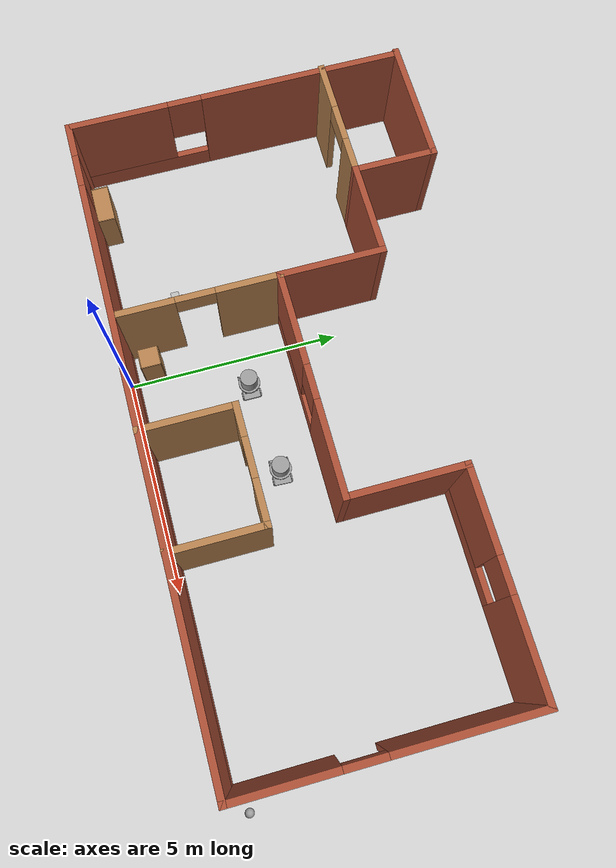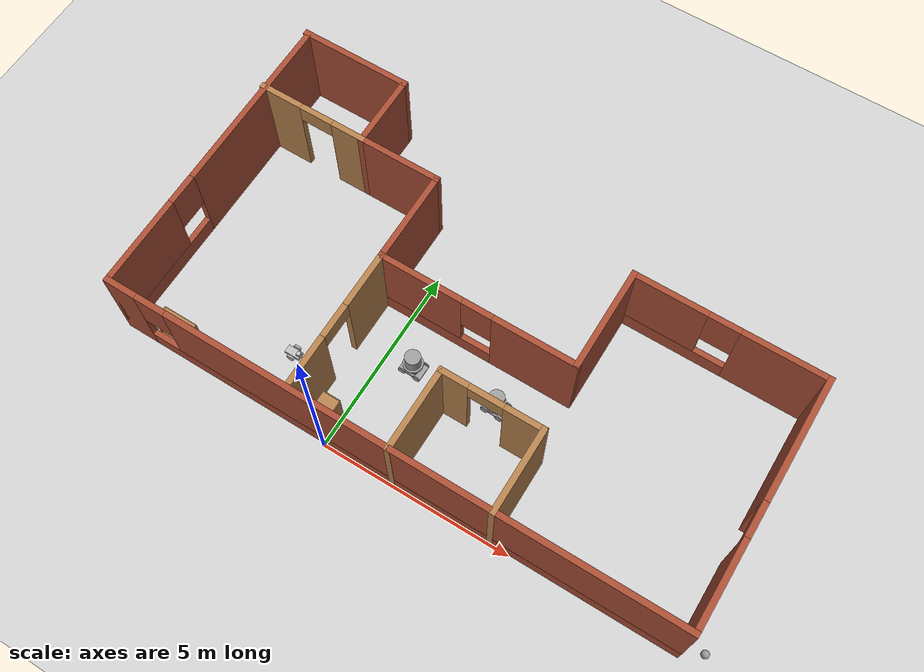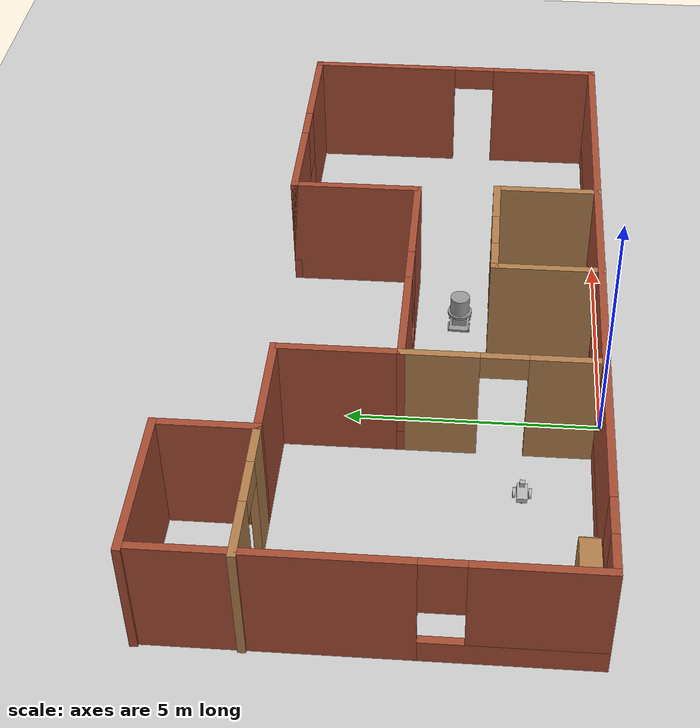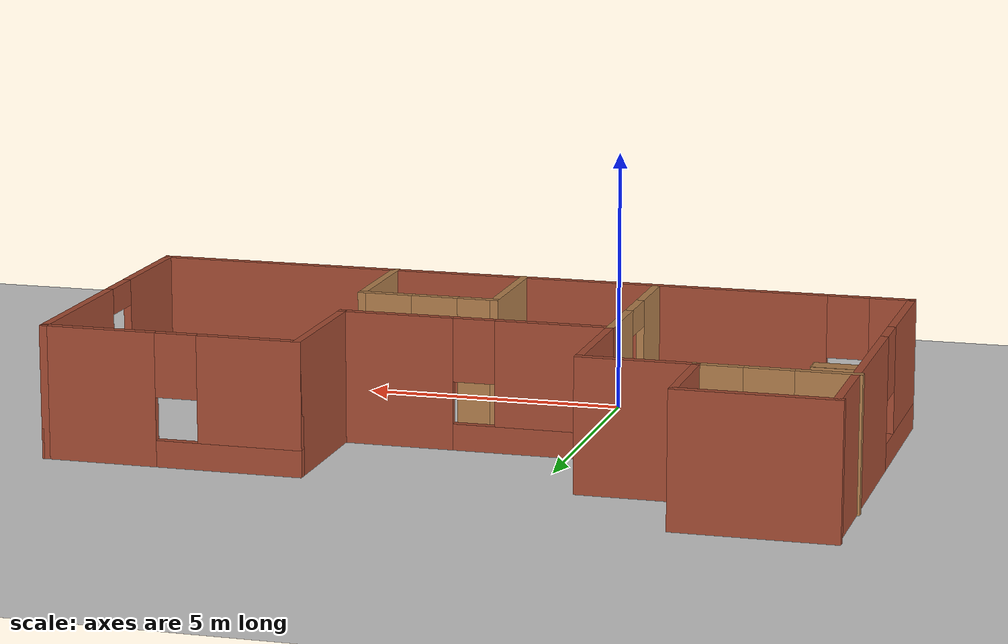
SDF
<sdf version="1.6">
 <world name="default">
  <plugin name="hello" filename="libhello.so"/>
  <light name="sun" type="directional">
   <pose>0 0 10 0 -0 0</pose>
   <diffuse>0.8 0.8 0.8 1</diffuse>
   <specular>0.2 0.2 0.2 1</specular>
   <attenuation>
    <range>1000</range>
    <constant>0.9</constant>
    <linear>0.01</linear>
    <quadratic>0.001</quadratic>
   </attenuation>
   <direction>-0.5 0.1 -0.9</direction>
  </light>
  <model name="ground_plane">
   <static>1</static>
   <link name="link">
    <collision name="collision">
     <geometry><plane><normal>0 0 1</normal><size>100 100</size></plane></geometry>
     <surface>
      <contact><collide_bitmask>65535</collide_bitmask></contact>
      <friction><ode><mu>100</mu><mu2>50</mu2></ode></friction>
     </surface>
    </collision>
    <visual name="visual">
     <cast_shadows>0</cast_shadows>
     <geometry><plane><normal>0 0 1</normal><size>100 100</size></plane></geometry>
     <material>
      <script><uri>file://media/materials/scripts/gazebo.material</uri><name>Gazebo/Grey</name></script>
     </material>
    </visual>
   </link>
  </model>
  <gravity>0 0 -9.8</gravity>
  <magnetic_field>6e-06 2.3e-05 -4.2e-05</magnetic_field>
  <atmosphere type="adiabatic"/>
  <physics name="default_physics" default="0" type="ode">
   <max_step_size>0.001</max_step_size>
   <real_time_factor>1</real_time_factor>
   <real_time_update_rate>1000</real_time_update_rate>
  </physics>
  <scene><ambient>0.4 0.4 0.4 1</ambient><background>0.7 0.7 0.7 1</background><shadows>1</shadows></scene>
  <spherical_coordinates>
   <surface_model>EARTH_WGS84</surface_model>
   <latitude_deg>0</latitude_deg>
   <longitude_deg>0</longitude_deg>
   <elevation>0</elevation>
   <heading_deg>0</heading_deg>
  </spherical_coordinates>
  <model name="School">
   <pose>1.72931 4.07996 0 0 -0 0</pose>
   <link name="Wall_10">
    <collision name="Wall_10_Collision">
     <geometry><box><size>2.25 0.15 2.5</size></box></geometry>
     <pose>0 0 1.25 0 -0 0</pose>
    </collision>
    <visual name="Wall_10_Visual">
     <pose>0 0 1.25 0 -0 0</pose>
     <geometry><box><size>2.25 0.15 2.5</size></box></geometry>
     <material>
      <script><uri>file://media/materials/scripts/gazebo.material</uri><name>Gazebo/Bricks</name></script>
      <ambient>1 1 1 1</ambient>
     </material>
     <meta><layer>0</layer></meta>
    </visual>
    <pose>-3.55 2.12783 0 0 -0 3.14159</pose>
   </link>
   <link name="Wall_15">
    <collision name="Wall_15_Collision">
     <geometry><box><size>2 0.15 2.5</size></box></geometry>
     <pose>0 0 1.25 0 -0 0</pose>
    </collision>
    <visual name="Wall_15_Visual">
     <pose>0 0 1.25 0 -0 0</pose>
     <geometry><box><size>2 0.15 2.5</size></box></geometry>
     <material>
      <script><uri>file://media/materials/scripts/gazebo.material</uri><name>Gazebo/Bricks</name></script>
      <ambient>1 1 1 1</ambient>
     </material>
     <meta><layer>0</layer></meta>
    </visual>
    <pose>-4.6 3.05282 0 0 -0 1.5708</pose>
   </link>
   <link name="Wall_16">
    <collision name="Wall_16_Collision">
     <geometry><box><size>3 0.15 2.5</size></box></geometry>
     <pose>0 0 1.25 0 -0 0</pose>
    </collision>
    <visual name="Wall_16_Visual">
     <pose>0 0 1.25 0 -0 0</pose>
     <geometry><box><size>3 0.15 2.5</size></box></geometry>
     <material>
      <script><uri>file://media/materials/scripts/gazebo.material</uri><name>Gazebo/Bricks</name></script>
      <ambient>1 1 1 1</ambient>
     </material>
     <meta><layer>0</layer></meta>
    </visual>
    <pose>-6.025 3.97783 0 0 -0 3.14159</pose>
   </link>
   <link name="Wall_21">
    <pose>-6.025 2.12783 0 0 -0 3.14159</pose>
    <visual name="Wall_21_Visual_0">
     <pose>-1.04133 0 1.25 0 -0 0</pose>
     <geometry><box><size>0.91735 0.15 2.5</size></box></geometry>
     <material>
      <script><uri>file://media/materials/scripts/gazebo.material</uri><name>Gazebo/Wood</name></script>
      <ambient>1 1 1 1</ambient>
     </material>
     <meta><layer>0</layer></meta>
    </visual>
    <collision name="Wall_21_Collision_0">
     <geometry><box><size>0.91735 0.15 2.5</size></box></geometry>
     <pose>-1.04133 0 1.25 0 -0 0</pose>
    </collision>
    <visual name="Wall_21_Visual_1">
     <pose>0.908675 0 1.25 0 -0 0</pose>
     <geometry><box><size>1.18265 0.15 2.5</size></box></geometry>
     <material>
      <script><uri>file://media/materials/scripts/gazebo.material</uri><name>Gazebo/Wood</name></script>
      <ambient>1 1 1 1</ambient>
     </material>
     <meta><layer>0</layer></meta>
    </visual>
    <collision name="Wall_21_Collision_1">
     <geometry><box><size>1.18265 0.15 2.5</size></box></geometry>
     <pose>0.908675 0 1.25 0 -0 0</pose>
    </collision>
    <visual name="Wall_21_Visual_2">
     <pose>-0.13265 0 2.25 0 -0 0</pose>
     <geometry><box><size>0.9 0.15 0.5</size></box></geometry>
     <material>
      <script><uri>file://media/materials/scripts/gazebo.material</uri><name>Gazebo/Wood</name></script>
      <ambient>1 1 1 1</ambient>
     </material>
     <meta><layer>0</layer></meta>
    </visual>
    <collision name="Wall_21_Collision_2">
     <geometry><box><size>0.9 0.15 0.5</size></box></geometry>
     <pose>-0.13265 0 2.25 0 -0 0</pose>
    </collision>
   </link>
   <link name="Wall_23">
    <pose>-2.5 -2.02217 0 0 0 -1.5708</pose>
    <visual name="Wall_23_Visual_0">
     <pose>-1.11042 0 1.25 0 -0 0</pose>
     <geometry><box><size>1.52915 0.15 2.5</size></box></geometry>
     <material>
      <script><uri>file://media/materials/scripts/gazebo.material</uri><name>Gazebo/Wood</name></script>
      <ambient>1 1 1 1</ambient>
     </material>
     <meta><layer>0</layer></meta>
    </visual>
    <collision name="Wall_23_Collision_0">
     <geometry><box><size>1.52915 0.15 2.5</size></box></geometry>
     <pose>-1.11042 0 1.25 0 -0 0</pose>
    </collision>
    <visual name="Wall_23_Visual_1">
     <pose>1.21457 0 1.25 0 -0 0</pose>
     <geometry><box><size>1.32085 0.15 2.5</size></box></geometry>
     <material>
      <script><uri>file://media/materials/scripts/gazebo.material</uri><name>Gazebo/Wood</name></script>
      <ambient>1 1 1 1</ambient>
     </material>
     <meta><layer>0</layer></meta>
    </visual>
    <collision name="Wall_23_Collision_1">
     <geometry><box><size>1.32085 0.15 2.5</size></box></geometry>
     <pose>1.21457 0 1.25 0 -0 0</pose>
    </collision>
    <visual name="Wall_23_Visual_2">
     <pose>0.10415 0 2.25 0 -0 0</pose>
     <geometry><box><size>0.9 0.15 0.5</size></box></geometry>
     <material>
      <script><uri>file://media/materials/scripts/gazebo.material</uri><name>Gazebo/Wood</name></script>
      <ambient>1 1 1 1</ambient>
     </material>
     <meta><layer>0</layer></meta>
    </visual>
    <collision name="Wall_23_Collision_2">
     <geometry><box><size>0.9 0.15 0.5</size></box></geometry>
     <pose>0.10415 0 2.25 0 -0 0</pose>
    </collision>
   </link>
   <link name="Wall_25">
    <collision name="Wall_25_Collision">
     <geometry><box><size>2.25 0.15 2.5</size></box></geometry>
     <pose>0 0 1.25 0 -0 0</pose>
    </collision>
    <visual name="Wall_25_Visual">
     <pose>0 0 1.25 0 -0 0</pose>
     <geometry><box><size>2.25 0.15 2.5</size></box></geometry>
     <material>
      <script><uri>file://media/materials/scripts/gazebo.material</uri><name>Gazebo/Wood</name></script>
      <ambient>1 1 1 1</ambient>
     </material>
     <meta><layer>0</layer></meta>
    </visual>
    <pose>0.13825 -2.92782 0 0 -0 1.5708</pose>
   </link>
   <link name="Wall_26">
    <pose>1.43825 -1.87783 0 0 -0 0</pose>
    <visual name="Wall_26_Visual_0">
     <pose>-0.9806 0 1.25 0 -0 0</pose>
     <geometry><box><size>0.7888 0.15 2.5</size></box></geometry>
     <material>
      <script><uri>file://media/materials/scripts/gazebo.material</uri><name>Gazebo/Wood</name></script>
      <ambient>1 1 1 1</ambient>
     </material>
     <meta><layer>0</layer></meta>
    </visual>
    <collision name="Wall_26_Collision_0">
     <geometry><box><size>0.7888 0.15 2.5</size></box></geometry>
     <pose>-0.9806 0 1.25 0 -0 0</pose>
    </collision>
    <visual name="Wall_26_Visual_1">
     <pose>0.8444 0 1.25 0 -0 0</pose>
     <geometry><box><size>1.0612 0.15 2.5</size></box></geometry>
     <material>
      <script><uri>file://media/materials/scripts/gazebo.material</uri><name>Gazebo/Wood</name></script>
      <ambient>1 1 1 1</ambient>
     </material>
     <meta><layer>0</layer></meta>
    </visual>
    <collision name="Wall_26_Collision_1">
     <geometry><box><size>1.0612 0.15 2.5</size></box></geometry>
     <pose>0.8444 0 1.25 0 -0 0</pose>
    </collision>
    <visual name="Wall_26_Visual_2">
     <pose>-0.1362 0 2.25 0 -0 0</pose>
     <geometry><box><size>0.9 0.15 0.5</size></box></geometry>
     <material>
      <script><uri>file://media/materials/scripts/gazebo.material</uri><name>Gazebo/Wood</name></script>
      <ambient>1 1 1 1</ambient>
     </material>
     <meta><layer>0</layer></meta>
    </visual>
    <collision name="Wall_26_Collision_2">
     <geometry><box><size>0.9 0.15 0.5</size></box></geometry>
     <pose>-0.1362 0 2.25 0 -0 0</pose>
    </collision>
   </link>
   <link name="Wall_27">
    <collision name="Wall_27_Collision">
     <geometry><box><size>2.25 0.15 2.5</size></box></geometry>
     <pose>0 0 1.25 0 -0 0</pose>
    </collision>
    <visual name="Wall_27_Visual">
     <pose>0 0 1.25 0 -0 0</pose>
     <geometry><box><size>2.25 0.15 2.5</size></box></geometry>
     <material>
      <script><uri>file://media/materials/scripts/gazebo.material</uri><name>Gazebo/Wood</name></script>
      <ambient>1 1 1 1</ambient>
     </material>
     <meta><layer>0</layer></meta>
    </visual>
    <pose>2.73825 -2.92782 0 0 0 -1.5708</pose>
   </link>
   <link name="Wall_3">
    <pose>-7.4 -0.047175 0 0 0 -1.5708</pose>
    <visual name="Wall_3_Visual_0">
     <pose>-1.61007 0 1.25 0 -0 0</pose>
     <geometry><box><size>4.77985 0.15 2.5</size></box></geometry>
     <material>
      <script><uri>file://media/materials/scripts/gazebo.material</uri><name>Gazebo/Bricks</name></script>
      <ambient>1 1 1 1</ambient>
     </material>
     <meta><layer>0</layer></meta>
    </visual>
    <collision name="Wall_3_Collision_0">
     <geometry><box><size>4.77985 0.15 2.5</size></box></geometry>
     <pose>-1.61007 0 1.25 0 -0 0</pose>
    </collision>
    <visual name="Wall_3_Visual_1">
     <pose>2.38992 0 0.25 0 -0 0</pose>
     <geometry><box><size>3.22015 0.15 0.5</size></box></geometry>
     <material>
      <script><uri>file://media/materials/scripts/gazebo.material</uri><name>Gazebo/Bricks</name></script>
      <ambient>1 1 1 1</ambient>
     </material>
     <meta><layer>0</layer></meta>
    </visual>
    <collision name="Wall_3_Collision_1">
     <geometry><box><size>3.22015 0.15 0.5</size></box></geometry>
     <pose>2.38992 0 0.25 0 -0 0</pose>
    </collision>
    <visual name="Wall_3_Visual_2">
     <pose>2.78993 0 1.5 0 -0 0</pose>
     <geometry><box><size>2.42015 0.15 2</size></box></geometry>
     <material>
      <script><uri>file://media/materials/scripts/gazebo.material</uri><name>Gazebo/Bricks</name></script>
      <ambient>1 1 1 1</ambient>
     </material>
     <meta><layer>0</layer></meta>
    </visual>
    <collision name="Wall_3_Collision_2">
     <geometry><box><size>2.42015 0.15 2</size></box></geometry>
     <pose>2.78993 0 1.5 0 -0 0</pose>
    </collision>
    <visual name="Wall_3_Visual_3">
     <pose>1.17985 0 1.9 0 -0 0</pose>
     <geometry><box><size>0.8 0.15 1.2</size></box></geometry>
     <material>
      <script><uri>file://media/materials/scripts/gazebo.material</uri><name>Gazebo/Bricks</name></script>
      <ambient>1 1 1 1</ambient>
     </material>
     <meta><layer>0</layer></meta>
    </visual>
    <collision name="Wall_3_Collision_3">
     <geometry><box><size>0.8 0.15 1.2</size></box></geometry>
     <pose>1.17985 0 1.9 0 -0 0</pose>
    </collision>
   </link>
   <link name="Wall_4">
    <pose>0.024999 -3.97218 0 0 -0 0</pose>
    <visual name="Wall_4_Visual_0">
     <pose>-7.06738 0 1.25 0 -0 0</pose>
     <geometry><box><size>0.86525 0.15 2.5</size></box></geometry>
     <material>
      <script><uri>file://media/materials/scripts/gazebo.material</uri><name>Gazebo/Bricks</name></script>
      <ambient>1 1 1 1</ambient>
     </material>
     <meta><layer>0</layer></meta>
    </visual>
    <collision name="Wall_4_Collision_0">
     <geometry><box><size>0.86525 0.15 2.5</size></box></geometry>
     <pose>-7.06738 0 1.25 0 -0 0</pose>
    </collision>
    <visual name="Wall_4_Visual_1">
     <pose>0.432625 0 0.25 0 -0 0</pose>
     <geometry><box><size>14.1348 0.15 0.5</size></box></geometry>
     <material>
      <script><uri>file://media/materials/scripts/gazebo.material</uri><name>Gazebo/Bricks</name></script>
      <ambient>1 1 1 1</ambient>
     </material>
     <meta><layer>0</layer></meta>
    </visual>
    <collision name="Wall_4_Collision_1">
     <geometry><box><size>14.1348 0.15 0.5</size></box></geometry>
     <pose>0.432625 0 0.25 0 -0 0</pose>
    </collision>
    <visual name="Wall_4_Visual_2">
     <pose>0.832625 0 1.5 0 -0 0</pose>
     <geometry><box><size>13.3347 0.15 2</size></box></geometry>
     <material>
      <script><uri>file://media/materials/scripts/gazebo.material</uri><name>Gazebo/Bricks</name></script>
      <ambient>1 1 1 1</ambient>
     </material>
     <meta><layer>0</layer></meta>
    </visual>
    <collision name="Wall_4_Collision_2">
     <geometry><box><size>13.3347 0.15 2</size></box></geometry>
     <pose>0.832625 0 1.5 0 -0 0</pose>
    </collision>
    <visual name="Wall_4_Visual_3">
     <pose>-6.23475 0 1.9 0 -0 0</pose>
     <geometry><box><size>0.8 0.15 1.2</size></box></geometry>
     <material>
      <script><uri>file://media/materials/scripts/gazebo.material</uri><name>Gazebo/Bricks</name></script>
      <ambient>1 1 1 1</ambient>
     </material>
     <meta><layer>0</layer></meta>
    </visual>
    <collision name="Wall_4_Collision_3">
     <geometry><box><size>0.8 0.15 1.2</size></box></geometry>
     <pose>-6.23475 0 1.9 0 -0 0</pose>
    </collision>
   </link>
   <link name="Wall_5">
    <pose>7.45 -0.797175 0 0 -0 1.5708</pose>
    <visual name="Wall_5_Visual_0">
     <pose>-2.07815 0 1.25 0 -0 0</pose>
     <geometry><box><size>2.3437 0.15 2.5</size></box></geometry>
     <material>
      <script><uri>file://media/materials/scripts/gazebo.material</uri><name>Gazebo/Bricks</name></script>
      <ambient>0.435294 0.796078 0.67451 1</ambient>
     </material>
     <meta><layer>0</layer></meta>
    </visual>
    <collision name="Wall_5_Collision_0">
     <geometry><box><size>2.3437 0.15 2.5</size></box></geometry>
     <pose>-2.07815 0 1.25 0 -0 0</pose>
    </collision>
    <visual name="Wall_5_Visual_1">
     <pose>1.62185 0 1.25 0 -0 0</pose>
     <geometry><box><size>3.2563 0.15 2.5</size></box></geometry>
     <material>
      <script><uri>file://media/materials/scripts/gazebo.material</uri><name>Gazebo/Bricks</name></script>
      <ambient>0.435294 0.796078 0.67451 1</ambient>
     </material>
     <meta><layer>0</layer></meta>
    </visual>
    <collision name="Wall_5_Collision_1">
     <geometry><box><size>3.2563 0.15 2.5</size></box></geometry>
     <pose>1.62185 0 1.25 0 -0 0</pose>
    </collision>
    <visual name="Wall_5_Visual_2">
     <pose>-0.4563 0 2.25 0 -0 0</pose>
     <geometry><box><size>0.9 0.15 0.5</size></box></geometry>
     <material>
      <script><uri>file://media/materials/scripts/gazebo.material</uri><name>Gazebo/Bricks</name></script>
      <ambient>0.435294 0.796078 0.67451 1</ambient>
     </material>
     <meta><layer>0</layer></meta>
    </visual>
    <collision name="Wall_5_Collision_2">
     <geometry><box><size>0.9 0.15 0.5</size></box></geometry>
     <pose>-0.4563 0 2.25 0 -0 0</pose>
    </collision>
   </link>
   <link name="Wall_6">
    <pose>5.025 2.37783 0 0 -0 3.14159</pose>
    <visual name="Wall_6_Visual_0">
     <pose>-1.38712 0 1.25 0 -0 0</pose>
     <geometry><box><size>2.22575 0.15 2.5</size></box></geometry>
     <material>
      <script><uri>file://media/materials/scripts/gazebo.material</uri><name>Gazebo/Bricks</name></script>
      <ambient>1 1 1 1</ambient>
     </material>
     <meta><layer>0</layer></meta>
    </visual>
    <collision name="Wall_6_Collision_0">
     <geometry><box><size>2.22575 0.15 2.5</size></box></geometry>
     <pose>-1.38712 0 1.25 0 -0 0</pose>
    </collision>
    <visual name="Wall_6_Visual_1">
     <pose>1.11288 0 0.25 0 -0 0</pose>
     <geometry><box><size>2.77425 0.15 0.5</size></box></geometry>
     <material>
      <script><uri>file://media/materials/scripts/gazebo.material</uri><name>Gazebo/Bricks</name></script>
      <ambient>1 1 1 1</ambient>
     </material>
     <meta><layer>0</layer></meta>
    </visual>
    <collision name="Wall_6_Collision_1">
     <geometry><box><size>2.77425 0.15 0.5</size></box></geometry>
     <pose>1.11288 0 0.25 0 -0 0</pose>
    </collision>
    <visual name="Wall_6_Visual_2">
     <pose>1.51287 0 1.5 0 -0 0</pose>
     <geometry><box><size>1.97425 0.15 2</size></box></geometry>
     <material>
      <script><uri>file://media/materials/scripts/gazebo.material</uri><name>Gazebo/Bricks</name></script>
      <ambient>1 1 1 1</ambient>
     </material>
     <meta><layer>0</layer></meta>
    </visual>
    <collision name="Wall_6_Collision_2">
     <geometry><box><size>1.97425 0.15 2</size></box></geometry>
     <pose>1.51287 0 1.5 0 -0 0</pose>
    </collision>
    <visual name="Wall_6_Visual_3">
     <pose>0.12575 0 1.9 0 -0 0</pose>
     <geometry><box><size>0.8 0.15 1.2</size></box></geometry>
     <material>
      <script><uri>file://media/materials/scripts/gazebo.material</uri><name>Gazebo/Bricks</name></script>
      <ambient>1 1 1 1</ambient>
     </material>
     <meta><layer>0</layer></meta>
    </visual>
    <collision name="Wall_6_Collision_3">
     <geometry><box><size>0.8 0.15 1.2</size></box></geometry>
     <pose>0.12575 0 1.9 0 -0 0</pose>
    </collision>
   </link>
   <link name="Wall_7">
    <collision name="Wall_7_Collision">
     <geometry><box><size>2.75 0.15 2.5</size></box></geometry>
     <pose>0 0 1.25 0 -0 0</pose>
    </collision>
    <visual name="Wall_7_Visual">
     <pose>0 0 1.25 0 -0 0</pose>
     <geometry><box><size>2.75 0.15 2.5</size></box></geometry>
     <material>
      <script><uri>file://media/materials/scripts/gazebo.material</uri><name>Gazebo/Bricks</name></script>
      <ambient>1 1 1 1</ambient>
     </material>
     <meta><layer>0</layer></meta>
    </visual>
    <pose>2.6 1.07783 0 0 0 -1.5708</pose>
   </link>
   <link name="Wall_8">
    <pose>0.05 -0.222175 0 0 -0 3.14159</pose>
    <visual name="Wall_8_Visual_0">
     <pose>-1.51695 0 1.25 0 -0 0</pose>
     <geometry><box><size>2.2161 0.15 2.5</size></box></geometry>
     <material>
      <script><uri>file://media/materials/scripts/gazebo.material</uri><name>Gazebo/Bricks</name></script>
      <ambient>1 1 1 1</ambient>
     </material>
     <meta><layer>0</layer></meta>
    </visual>
    <collision name="Wall_8_Collision_0">
     <geometry><box><size>2.2161 0.15 2.5</size></box></geometry>
     <pose>-1.51695 0 1.25 0 -0 0</pose>
    </collision>
    <visual name="Wall_8_Visual_1">
     <pose>1.10805 0 0.25 0 -0 0</pose>
     <geometry><box><size>3.0339 0.15 0.5</size></box></geometry>
     <material>
      <script><uri>file://media/materials/scripts/gazebo.material</uri><name>Gazebo/Bricks</name></script>
      <ambient>1 1 1 1</ambient>
     </material>
     <meta><layer>0</layer></meta>
    </visual>
    <collision name="Wall_8_Collision_1">
     <geometry><box><size>3.0339 0.15 0.5</size></box></geometry>
     <pose>1.10805 0 0.25 0 -0 0</pose>
    </collision>
    <visual name="Wall_8_Visual_2">
     <pose>1.50805 0 1.5 0 -0 0</pose>
     <geometry><box><size>2.2339 0.15 2</size></box></geometry>
     <material>
      <script><uri>file://media/materials/scripts/gazebo.material</uri><name>Gazebo/Bricks</name></script>
      <ambient>1 1 1 1</ambient>
     </material>
     <meta><layer>0</layer></meta>
    </visual>
    <collision name="Wall_8_Collision_2">
     <geometry><box><size>2.2339 0.15 2</size></box></geometry>
     <pose>1.50805 0 1.5 0 -0 0</pose>
    </collision>
    <visual name="Wall_8_Visual_3">
     <pose>-0.0089 0 1.9 0 -0 0</pose>
     <geometry><box><size>0.8 0.15 1.2</size></box></geometry>
     <material>
      <script><uri>file://media/materials/scripts/gazebo.material</uri><name>Gazebo/Bricks</name></script>
      <ambient>1 1 1 1</ambient>
     </material>
     <meta><layer>0</layer></meta>
    </visual>
    <collision name="Wall_8_Collision_3">
     <geometry><box><size>0.8 0.15 1.2</size></box></geometry>
     <pose>-0.0089 0 1.9 0 -0 0</pose>
    </collision>
   </link>
   <link name="Wall_9">
    <collision name="Wall_9_Collision">
     <geometry><box><size>2.5 0.15 2.5</size></box></geometry>
     <pose>0 0 1.25 0 -0 0</pose>
    </collision>
    <visual name="Wall_9_Visual">
     <pose>0 0 1.25 0 -0 0</pose>
     <geometry><box><size>2.5 0.15 2.5</size></box></geometry>
     <material>
      <script><uri>file://media/materials/scripts/gazebo.material</uri><name>Gazebo/Bricks</name></script>
      <ambient>1 1 1 1</ambient>
     </material>
     <meta><layer>0</layer></meta>
    </visual>
    <pose>-2.5 0.952825 0 0 -0 1.5708</pose>
   </link>
   <static>1</static>
  </model>
  <model name="4x4_robot">
   <link name="link_0">
    <pose>-0 0 -0.02 0 -0 0</pose>
    <inertial>
     <mass>1</mass>
     <inertia>
      <ixx>0.166667</ixx>
      <ixy>0</ixy>
      <ixz>0</ixz>
      <iyy>0.166667</iyy>
      <iyz>0</iyz>
      <izz>0.166667</izz>
     </inertia>
    </inertial>
    <visual name="visual">
     <geometry><box><size>0.6 0.4 0.05</size></box></geometry>
     <material>
      <lighting>1</lighting>
      <script><uri>file://media/materials/scripts/gazebo.material</uri><name>Gazebo/Grey</name></script>
      <shader type="pixel"><normal_map>__default__</normal_map></shader>
      <ambient>0.3 0.3 0.3 1</ambient>
      <diffuse>0.7 0.7 0.7 1</diffuse>
      <specular>0.01 0.01 0.01 1</specular>
      <emissive>0 0 0 1</emissive>
     </material>
    </visual>
    <collision name="collision">
     <geometry><box><size>0.6 0.4 0.05</size></box></geometry>
     <surface>
      <friction>
       <ode><mu>1</mu><mu2>1</mu2><fdir1>0 0 0</fdir1><slip1>0</slip1><slip2>0</slip2></ode>
       <torsional>
        <coefficient>1</coefficient>
        <patch_radius>0</patch_radius>
        <surface_radius>0</surface_radius>
        <use_patch_radius>1</use_patch_radius>
        <ode><slip>0</slip></ode>
       </torsional>
      </friction>
      <bounce><restitution_coefficient>0</restitution_coefficient><threshold>1e+06</threshold></bounce>
      <contact>
       <collide_without_contact>0</collide_without_contact>
       <collide_without_contact_bitmask>1</collide_without_contact_bitmask>
       <collide_bitmask>1</collide_bitmask>
       <ode>
        <soft_cfm>0</soft_cfm>
        <soft_erp>0.2</soft_erp>
        <kp>1e+13</kp>
        <kd>1</kd>
        <max_vel>0.01</max_vel>
        <min_depth>0</min_depth>
       </ode>
       <bullet>
        <split_impulse>1</split_impulse>
        <split_impulse_penetration_threshold>-0.01</split_impulse_penetration_threshold>
        <soft_cfm>0</soft_cfm>
        <soft_erp>0.2</soft_erp>
        <kp>1e+13</kp>
        <kd>1</kd>
       </bullet>
      </contact>
     </surface>
    </collision>
   </link>
   <link name="link_0_0">
    <pose>9.4e-05 1e-06 0.104673 2.5e-05 0.001086 0.029379</pose>
    <inertial>
     <mass>1</mass>
     <inertia>
      <ixx>0.166667</ixx>
      <ixy>0</ixy>
      <ixz>0</ixz>
      <iyy>0.166667</iyy>
      <iyz>0</iyz>
      <izz>0.166667</izz>
     </inertia>
    </inertial>
    <visual name="visual">
     <geometry><box><size>0.3 0.3 0.3</size></box></geometry>
     <material>
      <lighting>1</lighting>
      <script><uri>file://media/materials/scripts/gazebo.material</uri><name>Gazebo/Grey</name></script>
      <shader type="pixel"><normal_map>__default__</normal_map></shader>
      <ambient>0.3 0.3 0.3 1</ambient>
      <diffuse>0.7 0.7 0.7 1</diffuse>
      <specular>0.01 0.01 0.01 1</specular>
      <emissive>0 0 0 1</emissive>
     </material>
    </visual>
    <collision name="collision">
     <geometry><box><size>0.3 0.3 0.3</size></box></geometry>
     <surface>
      <friction>
       <ode><mu>1</mu><mu2>1</mu2><fdir1>0 0 0</fdir1><slip1>0</slip1><slip2>0</slip2></ode>
       <torsional>
        <coefficient>1</coefficient>
        <patch_radius>0</patch_radius>
        <surface_radius>0</surface_radius>
        <use_patch_radius>1</use_patch_radius>
        <ode><slip>0</slip></ode>
       </torsional>
      </friction>
      <bounce><restitution_coefficient>0</restitution_coefficient><threshold>1e+06</threshold></bounce>
      <contact>
       <collide_without_contact>0</collide_without_contact>
       <collide_without_contact_bitmask>1</collide_without_contact_bitmask>
       <collide_bitmask>1</collide_bitmask>
       <ode>
        <soft_cfm>0</soft_cfm>
        <soft_erp>0.2</soft_erp>
        <kp>1e+13</kp>
        <kd>1</kd>
        <max_vel>0.01</max_vel>
        <min_depth>0</min_depth>
       </ode>
       <bullet>
        <split_impulse>1</split_impulse>
        <split_impulse_penetration_threshold>-0.01</split_impulse_penetration_threshold>
        <soft_cfm>0</soft_cfm>
        <soft_erp>0.2</soft_erp>
        <kp>1e+13</kp>
        <kd>1</kd>
       </bullet>
      </contact>
     </surface>
    </collision>
   </link>
   <link name="link_1">
    <pose>0.2 0.2125 0.005 1.5708 -0 0</pose>
    <inertial>
     <mass>1</mass>
     <inertia><ixx>0.145833</ixx><ixy>0</ixy><ixz>0</ixz><iyy>0.145833</iyy><iyz>0</iyz><izz>0.125</izz></inertia>
    </inertial>
    <visual name="visual">
     <geometry><cylinder><radius>0.1</radius><length>0.025</length></cylinder></geometry>
     <material>
      <lighting>1</lighting>
      <script><uri>file://media/materials/scripts/gazebo.material</uri><name>Gazebo/Grey</name></script>
      <shader type="pixel"><normal_map>__default__</normal_map></shader>
      <ambient>0.3 0.3 0.3 1</ambient>
      <diffuse>0.7 0.7 0.7 1</diffuse>
      <specular>0.01 0.01 0.01 1</specular>
      <emissive>0 0 0 1</emissive>
     </material>
    </visual>
    <collision name="collision">
     <geometry><cylinder><radius>0.1</radius><length>0.025</length></cylinder></geometry>
     <surface>
      <friction>
       <ode><mu>1</mu><mu2>1</mu2><fdir1>0 0 0</fdir1><slip1>0</slip1><slip2>0</slip2></ode>
       <torsional>
        <coefficient>1</coefficient>
        <patch_radius>0</patch_radius>
        <surface_radius>0</surface_radius>
        <use_patch_radius>1</use_patch_radius>
        <ode><slip>0</slip></ode>
       </torsional>
      </friction>
      <bounce><restitution_coefficient>0</restitution_coefficient><threshold>1e+06</threshold></bounce>
      <contact>
       <collide_without_contact>0</collide_without_contact>
       <collide_without_contact_bitmask>1</collide_without_contact_bitmask>
       <collide_bitmask>1</collide_bitmask>
       <ode>
        <soft_cfm>0</soft_cfm>
        <soft_erp>0.2</soft_erp>
        <kp>1e+13</kp>
        <kd>1</kd>
        <max_vel>0.01</max_vel>
        <min_depth>0</min_depth>
       </ode>
       <bullet>
        <split_impulse>1</split_impulse>
        <split_impulse_penetration_threshold>-0.01</split_impulse_penetration_threshold>
        <soft_cfm>0</soft_cfm>
        <soft_erp>0.2</soft_erp>
        <kp>1e+13</kp>
        <kd>1</kd>
       </bullet>
      </contact>
     </surface>
    </collision>
   </link>
   <link name="link_1_0">
    <pose>0.000268 2e-06 0.264673 2.5e-05 0.001086 0.029379</pose>
    <inertial>
     <mass>1</mass>
     <inertia><ixx>0.145833</ixx><ixy>0</ixy><ixz>0</ixz><iyy>0.145833</iyy><iyz>0</iyz><izz>0.125</izz></inertia>
    </inertial>
    <visual name="visual">
     <geometry><cylinder><radius>0.25</radius><length>0.05</length></cylinder></geometry>
     <material>
      <lighting>1</lighting>
      <script><uri>file://media/materials/scripts/gazebo.material</uri><name>Gazebo/Grey</name></script>
      <shader type="pixel"><normal_map>__default__</normal_map></shader>
      <ambient>0.3 0.3 0.3 1</ambient>
      <diffuse>0.7 0.7 0.7 1</diffuse>
      <specular>0.01 0.01 0.01 1</specular>
      <emissive>0 0 0 1</emissive>
     </material>
    </visual>
    <collision name="collision">
     <geometry><cylinder><radius>0.25</radius><length>0.05</length></cylinder></geometry>
     <surface>
      <friction>
       <ode><mu>1</mu><mu2>1</mu2><fdir1>0 0 0</fdir1><slip1>0</slip1><slip2>0</slip2></ode>
       <torsional>
        <coefficient>1</coefficient>
        <patch_radius>0</patch_radius>
        <surface_radius>0</surface_radius>
        <use_patch_radius>1</use_patch_radius>
        <ode><slip>0</slip></ode>
       </torsional>
      </friction>
      <bounce><restitution_coefficient>0</restitution_coefficient><threshold>1e+06</threshold></bounce>
      <contact>
       <collide_without_contact>0</collide_without_contact>
       <collide_without_contact_bitmask>1</collide_without_contact_bitmask>
       <collide_bitmask>1</collide_bitmask>
       <ode>
        <soft_cfm>0</soft_cfm>
        <soft_erp>0.2</soft_erp>
        <kp>1e+13</kp>
        <kd>1</kd>
        <max_vel>0.01</max_vel>
        <min_depth>0</min_depth>
       </ode>
       <bullet>
        <split_impulse>1</split_impulse>
        <split_impulse_penetration_threshold>-0.01</split_impulse_penetration_threshold>
        <soft_cfm>0</soft_cfm>
        <soft_erp>0.2</soft_erp>
        <kp>1e+13</kp>
        <kd>1</kd>
       </bullet>
      </contact>
     </surface>
    </collision>
   </link>
   <link name="link_1_clone">
    <pose>-0.2 -0.2125 0.005 1.5708 -0 0</pose>
    <inertial>
     <mass>1</mass>
     <inertia><ixx>0.145833</ixx><ixy>0</ixy><ixz>0</ixz><iyy>0.145833</iyy><iyz>0</iyz><izz>0.125</izz></inertia>
    </inertial>
    <visual name="visual">
     <geometry><cylinder><radius>0.1</radius><length>0.025</length></cylinder></geometry>
     <material>
      <lighting>1</lighting>
      <script><uri>file://media/materials/scripts/gazebo.material</uri><name>Gazebo/Grey</name></script>
      <shader type="pixel"><normal_map>__default__</normal_map></shader>
      <ambient>0.3 0.3 0.3 1</ambient>
      <diffuse>0.7 0.7 0.7 1</diffuse>
      <specular>0.01 0.01 0.01 1</specular>
      <emissive>0 0 0 1</emissive>
     </material>
    </visual>
    <collision name="collision">
     <geometry><cylinder><radius>0.1</radius><length>0.025</length></cylinder></geometry>
     <surface>
      <friction>
       <ode><mu>1</mu><mu2>1</mu2><fdir1>0 0 0</fdir1><slip1>0</slip1><slip2>0</slip2></ode>
       <torsional>
        <coefficient>1</coefficient>
        <patch_radius>0</patch_radius>
        <surface_radius>0</surface_radius>
        <use_patch_radius>1</use_patch_radius>
        <ode><slip>0</slip></ode>
       </torsional>
      </friction>
      <bounce><restitution_coefficient>0</restitution_coefficient><threshold>1e+06</threshold></bounce>
      <contact>
       <collide_without_contact>0</collide_without_contact>
       <collide_without_contact_bitmask>1</collide_without_contact_bitmask>
       <collide_bitmask>1</collide_bitmask>
       <ode>
        <soft_cfm>0</soft_cfm>
        <soft_erp>0.2</soft_erp>
        <kp>1e+13</kp>
        <kd>1</kd>
        <max_vel>0.01</max_vel>
        <min_depth>0</min_depth>
       </ode>
       <bullet>
        <split_impulse>1</split_impulse>
        <split_impulse_penetration_threshold>-0.01</split_impulse_penetration_threshold>
        <soft_cfm>0</soft_cfm>
        <soft_erp>0.2</soft_erp>
        <kp>1e+13</kp>
        <kd>1</kd>
       </bullet>
      </contact>
     </surface>
    </collision>
   </link>
   <link name="link_1_clone_0">
    <pose>-0.2 0.2125 0.005 1.5708 -0 0</pose>
    <inertial>
     <mass>1</mass>
     <inertia><ixx>0.145833</ixx><ixy>0</ixy><ixz>0</ixz><iyy>0.145833</iyy><iyz>0</iyz><izz>0.125</izz></inertia>
    </inertial>
    <visual name="visual">
     <geometry><cylinder><radius>0.1</radius><length>0.025</length></cylinder></geometry>
     <material>
      <lighting>1</lighting>
      <script><uri>file://media/materials/scripts/gazebo.material</uri><name>Gazebo/Grey</name></script>
      <shader type="pixel"><normal_map>__default__</normal_map></shader>
      <ambient>0.3 0.3 0.3 1</ambient>
      <diffuse>0.7 0.7 0.7 1</diffuse>
      <specular>0.01 0.01 0.01 1</specular>
      <emissive>0 0 0 1</emissive>
     </material>
    </visual>
    <collision name="collision">
     <geometry><cylinder><radius>0.1</radius><length>0.025</length></cylinder></geometry>
     <surface>
      <friction>
       <ode><mu>1</mu><mu2>1</mu2><fdir1>0 0 0</fdir1><slip1>0</slip1><slip2>0</slip2></ode>
       <torsional>
        <coefficient>1</coefficient>
        <patch_radius>0</patch_radius>
        <surface_radius>0</surface_radius>
        <use_patch_radius>1</use_patch_radius>
        <ode><slip>0</slip></ode>
       </torsional>
      </friction>
      <bounce><restitution_coefficient>0</restitution_coefficient><threshold>1e+06</threshold></bounce>
      <contact>
       <collide_without_contact>0</collide_without_contact>
       <collide_without_contact_bitmask>1</collide_without_contact_bitmask>
       <collide_bitmask>1</collide_bitmask>
       <ode>
        <soft_cfm>0</soft_cfm>
        <soft_erp>0.2</soft_erp>
        <kp>1e+13</kp>
        <kd>1</kd>
        <max_vel>0.01</max_vel>
        <min_depth>0</min_depth>
       </ode>
       <bullet>
        <split_impulse>1</split_impulse>
        <split_impulse_penetration_threshold>-0.01</split_impulse_penetration_threshold>
        <soft_cfm>0</soft_cfm>
        <soft_erp>0.2</soft_erp>
        <kp>1e+13</kp>
        <kd>1</kd>
       </bullet>
      </contact>
     </surface>
    </collision>
   </link>
   <link name="link_1_clone_1">
    <pose>0.2 -0.2125 0.005 1.5708 -0 0</pose>
    <inertial>
     <mass>1</mass>
     <inertia><ixx>0.145833</ixx><ixy>0</ixy><ixz>0</ixz><iyy>0.145833</iyy><iyz>0</iyz><izz>0.125</izz></inertia>
    </inertial>
    <visual name="visual">
     <geometry><cylinder><radius>0.1</radius><length>0.025</length></cylinder></geometry>
     <material>
      <lighting>1</lighting>
      <script><uri>file://media/materials/scripts/gazebo.material</uri><name>Gazebo/Grey</name></script>
      <shader type="pixel"><normal_map>__default__</normal_map></shader>
      <ambient>0.3 0.3 0.3 1</ambient>
      <diffuse>0.7 0.7 0.7 1</diffuse>
      <specular>0.01 0.01 0.01 1</specular>
      <emissive>0 0 0 1</emissive>
     </material>
    </visual>
    <collision name="collision">
     <geometry><cylinder><radius>0.1</radius><length>0.025</length></cylinder></geometry>
     <surface>
      <friction>
       <ode><mu>1</mu><mu2>1</mu2><fdir1>0 0 0</fdir1><slip1>0</slip1><slip2>0</slip2></ode>
       <torsional>
        <coefficient>1</coefficient>
        <patch_radius>0</patch_radius>
        <surface_radius>0</surface_radius>
        <use_patch_radius>1</use_patch_radius>
        <ode><slip>0</slip></ode>
       </torsional>
      </friction>
      <bounce><restitution_coefficient>0</restitution_coefficient><threshold>1e+06</threshold></bounce>
      <contact>
       <collide_without_contact>0</collide_without_contact>
       <collide_without_contact_bitmask>1</collide_without_contact_bitmask>
       <collide_bitmask>1</collide_bitmask>
       <ode>
        <soft_cfm>0</soft_cfm>
        <soft_erp>0.2</soft_erp>
        <kp>1e+13</kp>
        <kd>1</kd>
        <max_vel>0.01</max_vel>
        <min_depth>0</min_depth>
       </ode>
       <bullet>
        <split_impulse>1</split_impulse>
        <split_impulse_penetration_threshold>-0.01</split_impulse_penetration_threshold>
        <soft_cfm>0</soft_cfm>
        <soft_erp>0.2</soft_erp>
        <kp>1e+13</kp>
        <kd>1</kd>
       </bullet>
      </contact>
     </surface>
    </collision>
   </link>
   <link name="link_2">
    <pose>0.000485 4e-06 0.464673 2.5e-05 0.001086 0.029379</pose>
    <inertial>
     <mass>1</mass>
     <inertia><ixx>0.145833</ixx><ixy>0</ixy><ixz>0</ixz><iyy>0.145833</iyy><iyz>0</iyz><izz>0.125</izz></inertia>
    </inertial>
    <visual name="visual">
     <geometry><cylinder><radius>0.2</radius><length>0.4</length></cylinder></geometry>
     <material>
      <lighting>1</lighting>
      <script><uri>file://media/materials/scripts/gazebo.material</uri><name>Gazebo/Grey</name></script>
      <shader type="pixel"><normal_map>__default__</normal_map></shader>
      <ambient>0.3 0.3 0.3 1</ambient>
      <diffuse>0.7 0.7 0.7 1</diffuse>
      <specular>0.01 0.01 0.01 1</specular>
      <emissive>0 0 0 1</emissive>
     </material>
    </visual>
    <collision name="collision">
     <geometry><cylinder><radius>0.2</radius><length>0.4</length></cylinder></geometry>
     <surface>
      <friction>
       <ode><mu>1</mu><mu2>1</mu2><fdir1>0 0 0</fdir1><slip1>0</slip1><slip2>0</slip2></ode>
       <torsional>
        <coefficient>1</coefficient>
        <patch_radius>0</patch_radius>
        <surface_radius>0</surface_radius>
        <use_patch_radius>1</use_patch_radius>
        <ode><slip>0</slip></ode>
       </torsional>
      </friction>
      <bounce><restitution_coefficient>0</restitution_coefficient><threshold>1e+06</threshold></bounce>
      <contact>
       <collide_without_contact>0</collide_without_contact>
       <collide_without_contact_bitmask>1</collide_without_contact_bitmask>
       <collide_bitmask>1</collide_bitmask>
       <ode>
        <soft_cfm>0</soft_cfm>
        <soft_erp>0.2</soft_erp>
        <kp>1e+13</kp>
        <kd>1</kd>
        <max_vel>0.01</max_vel>
        <min_depth>0</min_depth>
       </ode>
       <bullet>
        <split_impulse>1</split_impulse>
        <split_impulse_penetration_threshold>-0.01</split_impulse_penetration_threshold>
        <soft_cfm>0</soft_cfm>
        <soft_erp>0.2</soft_erp>
        <kp>1e+13</kp>
        <kd>1</kd>
       </bullet>
      </contact>
     </surface>
    </collision>
   </link>
   <joint name="link_0_0_JOINT_1" type="fixed">
    <parent>link_0_0</parent>
    <child>link_1_0</child>
    <physics>
     <ode><limit><cfm>0</cfm><erp>0.2</erp></limit><suspension><cfm>0</cfm><erp>0.2</erp></suspension></ode>
    </physics>
   </joint>
   <joint name="link_0_JOINT_0_0" type="fixed">
    <parent>link_0</parent>
    <child>link_0_0</child>
    <physics>
     <ode><limit><cfm>0</cfm><erp>0.2</erp></limit><suspension><cfm>0</cfm><erp>0.2</erp></suspension></ode>
    </physics>
   </joint>
   <joint name="link_0_JOINT_0" type="revolute">
    <parent>link_0</parent>
    <child>link_1_clone</child>
    <axis>
     <xyz>0 0 1</xyz>
     <use_parent_model_frame>0</use_parent_model_frame>
     <limit>
      <lower>-1.79769e+308</lower>
      <upper>1.79769e+308</upper>
      <effort>-1</effort>
      <velocity>-1</velocity>
     </limit>
     <dynamics>
      <spring_reference>0</spring_reference>
      <spring_stiffness>0</spring_stiffness>
      <damping>0</damping>
      <friction>0</friction>
     </dynamics>
    </axis>
    <physics>
     <ode><limit><cfm>0</cfm><erp>0.2</erp></limit><suspension><cfm>0</cfm><erp>0.2</erp></suspension></ode>
    </physics>
   </joint>
   <joint name="link_0_JOINT_1" type="revolute">
    <parent>link_0</parent>
    <child>link_1_clone_1</child>
    <axis>
     <xyz>0 0 1</xyz>
     <use_parent_model_frame>0</use_parent_model_frame>
     <limit>
      <lower>-1.79769e+308</lower>
      <upper>1.79769e+308</upper>
      <effort>-1</effort>
      <velocity>-1</velocity>
     </limit>
     <dynamics>
      <spring_reference>0</spring_reference>
      <spring_stiffness>0</spring_stiffness>
      <damping>0</damping>
      <friction>0</friction>
     </dynamics>
    </axis>
    <physics>
     <ode><limit><cfm>0</cfm><erp>0.2</erp></limit><suspension><cfm>0</cfm><erp>0.2</erp></suspension></ode>
    </physics>
   </joint>
   <joint name="link_0_JOINT_2" type="revolute">
    <parent>link_0</parent>
    <child>link_1_clone_0</child>
    <axis>
     <xyz>0 0 1</xyz>
     <use_parent_model_frame>0</use_parent_model_frame>
     <limit>
      <lower>-1.79769e+308</lower>
      <upper>1.79769e+308</upper>
      <effort>-1</effort>
      <velocity>-1</velocity>
     </limit>
     <dynamics>
      <spring_reference>0</spring_reference>
      <spring_stiffness>0</spring_stiffness>
      <damping>0</damping>
      <friction>0</friction>
     </dynamics>
    </axis>
    <physics>
     <ode><limit><cfm>0</cfm><erp>0.2</erp></limit><suspension><cfm>0</cfm><erp>0.2</erp></suspension></ode>
    </physics>
   </joint>
   <joint name="link_0_JOINT_7" type="revolute">
    <parent>link_0</parent>
    <child>link_1</child>
    <pose>0 0 0 0 -0.21 0</pose>
    <axis>
     <xyz>0 0 1</xyz>
     <use_parent_model_frame>0</use_parent_model_frame>
     <limit>
      <lower>-1.79769e+308</lower>
      <upper>1.79769e+308</upper>
      <effort>-1</effort>
      <velocity>-1</velocity>
     </limit>
     <dynamics>
      <spring_reference>0</spring_reference>
      <spring_stiffness>0</spring_stiffness>
      <damping>0</damping>
      <friction>0</friction>
     </dynamics>
    </axis>
    <physics>
     <ode><limit><cfm>0</cfm><erp>0.2</erp></limit><suspension><cfm>0</cfm><erp>0.2</erp></suspension></ode>
    </physics>
   </joint>
   <joint name="link_1_0_JOINT_2" type="revolute">
    <parent>link_1_0</parent>
    <child>link_2</child>
    <axis>
     <xyz>1 0 0</xyz>
     <use_parent_model_frame>0</use_parent_model_frame>
     <limit>
      <lower>-1.79769e+308</lower>
      <upper>1.79769e+308</upper>
      <effort>-1</effort>
      <velocity>-1</velocity>
     </limit>
     <dynamics>
      <spring_reference>0</spring_reference>
      <spring_stiffness>0</spring_stiffness>
      <damping>0</damping>
     </dynamics>
    </axis>
    <physics>
     <ode><limit><cfm>0</cfm><erp>0.2</erp></limit><suspension><cfm>0</cfm><erp>0.2</erp></suspension></ode>
    </physics>
   </joint>
   <static>0</static>
   <pose>2.93067 2.86948 0.095 0 0 -0.044799</pose>
  </model>
  <model name="4x4_robot_0">
   <link name="link_0">
    <pose>-0 0 -0.02 0 -0 0</pose>
    <inertial>
     <mass>1</mass>
     <inertia>
      <ixx>0.166667</ixx>
      <ixy>0</ixy>
      <ixz>0</ixz>
      <iyy>0.166667</iyy>
      <iyz>0</iyz>
      <izz>0.166667</izz>
     </inertia>
    </inertial>
    <visual name="visual">
     <geometry><box><size>0.6 0.4 0.05</size></box></geometry>
     <material>
      <lighting>1</lighting>
      <script><uri>file://media/materials/scripts/gazebo.material</uri><name>Gazebo/Grey</name></script>
      <shader type="pixel"><normal_map>__default__</normal_map></shader>
      <ambient>0.3 0.3 0.3 1</ambient>
      <diffuse>0.7 0.7 0.7 1</diffuse>
      <specular>0.01 0.01 0.01 1</specular>
      <emissive>0 0 0 1</emissive>
     </material>
    </visual>
    <collision name="collision">
     <geometry><box><size>0.6 0.4 0.05</size></box></geometry>
     <surface>
      <friction>
       <ode><mu>1</mu><mu2>1</mu2><fdir1>0 0 0</fdir1><slip1>0</slip1><slip2>0</slip2></ode>
       <torsional>
        <coefficient>1</coefficient>
        <patch_radius>0</patch_radius>
        <surface_radius>0</surface_radius>
        <use_patch_radius>1</use_patch_radius>
        <ode><slip>0</slip></ode>
       </torsional>
      </friction>
      <bounce><restitution_coefficient>0</restitution_coefficient><threshold>1e+06</threshold></bounce>
      <contact>
       <collide_without_contact>0</collide_without_contact>
       <collide_without_contact_bitmask>1</collide_without_contact_bitmask>
       <collide_bitmask>1</collide_bitmask>
       <ode>
        <soft_cfm>0</soft_cfm>
        <soft_erp>0.2</soft_erp>
        <kp>1e+13</kp>
        <kd>1</kd>
        <max_vel>0.01</max_vel>
        <min_depth>0</min_depth>
       </ode>
       <bullet>
        <split_impulse>1</split_impulse>
        <split_impulse_penetration_threshold>-0.01</split_impulse_penetration_threshold>
        <soft_cfm>0</soft_cfm>
        <soft_erp>0.2</soft_erp>
        <kp>1e+13</kp>
        <kd>1</kd>
       </bullet>
      </contact>
     </surface>
    </collision>
   </link>
   <link name="link_0_0">
    <pose>9.4e-05 1e-06 0.104673 2.5e-05 0.001086 0.029379</pose>
    <inertial>
     <mass>1</mass>
     <inertia>
      <ixx>0.166667</ixx>
      <ixy>0</ixy>
      <ixz>0</ixz>
      <iyy>0.166667</iyy>
      <iyz>0</iyz>
      <izz>0.166667</izz>
     </inertia>
    </inertial>
    <visual name="visual">
     <geometry><box><size>0.3 0.3 0.3</size></box></geometry>
     <material>
      <lighting>1</lighting>
      <script><uri>file://media/materials/scripts/gazebo.material</uri><name>Gazebo/Grey</name></script>
      <shader type="pixel"><normal_map>__default__</normal_map></shader>
      <ambient>0.3 0.3 0.3 1</ambient>
      <diffuse>0.7 0.7 0.7 1</diffuse>
      <specular>0.01 0.01 0.01 1</specular>
      <emissive>0 0 0 1</emissive>
     </material>
    </visual>
    <collision name="collision">
     <geometry><box><size>0.3 0.3 0.3</size></box></geometry>
     <surface>
      <friction>
       <ode><mu>1</mu><mu2>1</mu2><fdir1>0 0 0</fdir1><slip1>0</slip1><slip2>0</slip2></ode>
       <torsional>
        <coefficient>1</coefficient>
        <patch_radius>0</patch_radius>
        <surface_radius>0</surface_radius>
        <use_patch_radius>1</use_patch_radius>
        <ode><slip>0</slip></ode>
       </torsional>
      </friction>
      <bounce><restitution_coefficient>0</restitution_coefficient><threshold>1e+06</threshold></bounce>
      <contact>
       <collide_without_contact>0</collide_without_contact>
       <collide_without_contact_bitmask>1</collide_without_contact_bitmask>
       <collide_bitmask>1</collide_bitmask>
       <ode>
        <soft_cfm>0</soft_cfm>
        <soft_erp>0.2</soft_erp>
        <kp>1e+13</kp>
        <kd>1</kd>
        <max_vel>0.01</max_vel>
        <min_depth>0</min_depth>
       </ode>
       <bullet>
        <split_impulse>1</split_impulse>
        <split_impulse_penetration_threshold>-0.01</split_impulse_penetration_threshold>
        <soft_cfm>0</soft_cfm>
        <soft_erp>0.2</soft_erp>
        <kp>1e+13</kp>
        <kd>1</kd>
       </bullet>
      </contact>
     </surface>
    </collision>
   </link>
   <link name="link_1">
    <pose>0.2 0.2125 0.005 1.5708 -0 0</pose>
    <inertial>
     <mass>1</mass>
     <inertia><ixx>0.145833</ixx><ixy>0</ixy><ixz>0</ixz><iyy>0.145833</iyy><iyz>0</iyz><izz>0.125</izz></inertia>
    </inertial>
    <visual name="visual">
     <geometry><cylinder><radius>0.1</radius><length>0.025</length></cylinder></geometry>
     <material>
      <lighting>1</lighting>
      <script><uri>file://media/materials/scripts/gazebo.material</uri><name>Gazebo/Grey</name></script>
      <shader type="pixel"><normal_map>__default__</normal_map></shader>
      <ambient>0.3 0.3 0.3 1</ambient>
      <diffuse>0.7 0.7 0.7 1</diffuse>
      <specular>0.01 0.01 0.01 1</specular>
      <emissive>0 0 0 1</emissive>
     </material>
    </visual>
    <collision name="collision">
     <geometry><cylinder><radius>0.1</radius><length>0.025</length></cylinder></geometry>
     <surface>
      <friction>
       <ode><mu>1</mu><mu2>1</mu2><fdir1>0 0 0</fdir1><slip1>0</slip1><slip2>0</slip2></ode>
       <torsional>
        <coefficient>1</coefficient>
        <patch_radius>0</patch_radius>
        <surface_radius>0</surface_radius>
        <use_patch_radius>1</use_patch_radius>
        <ode><slip>0</slip></ode>
       </torsional>
      </friction>
      <bounce><restitution_coefficient>0</restitution_coefficient><threshold>1e+06</threshold></bounce>
      <contact>
       <collide_without_contact>0</collide_without_contact>
       <collide_without_contact_bitmask>1</collide_without_contact_bitmask>
       <collide_bitmask>1</collide_bitmask>
       <ode>
        <soft_cfm>0</soft_cfm>
        <soft_erp>0.2</soft_erp>
        <kp>1e+13</kp>
        <kd>1</kd>
        <max_vel>0.01</max_vel>
        <min_depth>0</min_depth>
       </ode>
       <bullet>
        <split_impulse>1</split_impulse>
        <split_impulse_penetration_threshold>-0.01</split_impulse_penetration_threshold>
        <soft_cfm>0</soft_cfm>
        <soft_erp>0.2</soft_erp>
        <kp>1e+13</kp>
        <kd>1</kd>
       </bullet>
      </contact>
     </surface>
    </collision>
   </link>
   <link name="link_1_0">
    <pose>0.000268 2e-06 0.264673 2.5e-05 0.001086 0.029379</pose>
    <inertial>
     <mass>1</mass>
     <inertia><ixx>0.145833</ixx><ixy>0</ixy><ixz>0</ixz><iyy>0.145833</iyy><iyz>0</iyz><izz>0.125</izz></inertia>
    </inertial>
    <visual name="visual">
     <geometry><cylinder><radius>0.25</radius><length>0.05</length></cylinder></geometry>
     <material>
      <lighting>1</lighting>
      <script><uri>file://media/materials/scripts/gazebo.material</uri><name>Gazebo/Grey</name></script>
      <shader type="pixel"><normal_map>__default__</normal_map></shader>
      <ambient>0.3 0.3 0.3 1</ambient>
      <diffuse>0.7 0.7 0.7 1</diffuse>
      <specular>0.01 0.01 0.01 1</specular>
      <emissive>0 0 0 1</emissive>
     </material>
    </visual>
    <collision name="collision">
     <geometry><cylinder><radius>0.25</radius><length>0.05</length></cylinder></geometry>
     <surface>
      <friction>
       <ode><mu>1</mu><mu2>1</mu2><fdir1>0 0 0</fdir1><slip1>0</slip1><slip2>0</slip2></ode>
       <torsional>
        <coefficient>1</coefficient>
        <patch_radius>0</patch_radius>
        <surface_radius>0</surface_radius>
        <use_patch_radius>1</use_patch_radius>
        <ode><slip>0</slip></ode>
       </torsional>
      </friction>
      <bounce><restitution_coefficient>0</restitution_coefficient><threshold>1e+06</threshold></bounce>
      <contact>
       <collide_without_contact>0</collide_without_contact>
       <collide_without_contact_bitmask>1</collide_without_contact_bitmask>
       <collide_bitmask>1</collide_bitmask>
       <ode>
        <soft_cfm>0</soft_cfm>
        <soft_erp>0.2</soft_erp>
        <kp>1e+13</kp>
        <kd>1</kd>
        <max_vel>0.01</max_vel>
        <min_depth>0</min_depth>
       </ode>
       <bullet>
        <split_impulse>1</split_impulse>
        <split_impulse_penetration_threshold>-0.01</split_impulse_penetration_threshold>
        <soft_cfm>0</soft_cfm>
        <soft_erp>0.2</soft_erp>
        <kp>1e+13</kp>
        <kd>1</kd>
       </bullet>
      </contact>
     </surface>
    </collision>
   </link>
   <link name="link_1_clone">
    <pose>-0.2 -0.2125 0.005 1.5708 -0 0</pose>
    <inertial>
     <mass>1</mass>
     <inertia><ixx>0.145833</ixx><ixy>0</ixy><ixz>0</ixz><iyy>0.145833</iyy><iyz>0</iyz><izz>0.125</izz></inertia>
    </inertial>
    <visual name="visual">
     <geometry><cylinder><radius>0.1</radius><length>0.025</length></cylinder></geometry>
     <material>
      <lighting>1</lighting>
      <script><uri>file://media/materials/scripts/gazebo.material</uri><name>Gazebo/Grey</name></script>
      <shader type="pixel"><normal_map>__default__</normal_map></shader>
      <ambient>0.3 0.3 0.3 1</ambient>
      <diffuse>0.7 0.7 0.7 1</diffuse>
      <specular>0.01 0.01 0.01 1</specular>
      <emissive>0 0 0 1</emissive>
     </material>
    </visual>
    <collision name="collision">
     <geometry><cylinder><radius>0.1</radius><length>0.025</length></cylinder></geometry>
     <surface>
      <friction>
       <ode><mu>1</mu><mu2>1</mu2><fdir1>0 0 0</fdir1><slip1>0</slip1><slip2>0</slip2></ode>
       <torsional>
        <coefficient>1</coefficient>
        <patch_radius>0</patch_radius>
        <surface_radius>0</surface_radius>
        <use_patch_radius>1</use_patch_radius>
        <ode><slip>0</slip></ode>
       </torsional>
      </friction>
      <bounce><restitution_coefficient>0</restitution_coefficient><threshold>1e+06</threshold></bounce>
      <contact>
       <collide_without_contact>0</collide_without_contact>
       <collide_without_contact_bitmask>1</collide_without_contact_bitmask>
       <collide_bitmask>1</collide_bitmask>
       <ode>
        <soft_cfm>0</soft_cfm>
        <soft_erp>0.2</soft_erp>
        <kp>1e+13</kp>
        <kd>1</kd>
        <max_vel>0.01</max_vel>
        <min_depth>0</min_depth>
       </ode>
       <bullet>
        <split_impulse>1</split_impulse>
        <split_impulse_penetration_threshold>-0.01</split_impulse_penetration_threshold>
        <soft_cfm>0</soft_cfm>
        <soft_erp>0.2</soft_erp>
        <kp>1e+13</kp>
        <kd>1</kd>
       </bullet>
      </contact>
     </surface>
    </collision>
   </link>
   <link name="link_1_clone_0">
    <pose>-0.2 0.2125 0.005 1.5708 -0 0</pose>
    <inertial>
     <mass>1</mass>
     <inertia><ixx>0.145833</ixx><ixy>0</ixy><ixz>0</ixz><iyy>0.145833</iyy><iyz>0</iyz><izz>0.125</izz></inertia>
    </inertial>
    <visual name="visual">
     <geometry><cylinder><radius>0.1</radius><length>0.025</length></cylinder></geometry>
     <material>
      <lighting>1</lighting>
      <script><uri>file://media/materials/scripts/gazebo.material</uri><name>Gazebo/Grey</name></script>
      <shader type="pixel"><normal_map>__default__</normal_map></shader>
      <ambient>0.3 0.3 0.3 1</ambient>
      <diffuse>0.7 0.7 0.7 1</diffuse>
      <specular>0.01 0.01 0.01 1</specular>
      <emissive>0 0 0 1</emissive>
     </material>
    </visual>
    <collision name="collision">
     <geometry><cylinder><radius>0.1</radius><length>0.025</length></cylinder></geometry>
     <surface>
      <friction>
       <ode><mu>1</mu><mu2>1</mu2><fdir1>0 0 0</fdir1><slip1>0</slip1><slip2>0</slip2></ode>
       <torsional>
        <coefficient>1</coefficient>
        <patch_radius>0</patch_radius>
        <surface_radius>0</surface_radius>
        <use_patch_radius>1</use_patch_radius>
        <ode><slip>0</slip></ode>
       </torsional>
      </friction>
      <bounce><restitution_coefficient>0</restitution_coefficient><threshold>1e+06</threshold></bounce>
      <contact>
       <collide_without_contact>0</collide_without_contact>
       <collide_without_contact_bitmask>1</collide_without_contact_bitmask>
       <collide_bitmask>1</collide_bitmask>
       <ode>
        <soft_cfm>0</soft_cfm>
        <soft_erp>0.2</soft_erp>
        <kp>1e+13</kp>
        <kd>1</kd>
        <max_vel>0.01</max_vel>
        <min_depth>0</min_depth>
       </ode>
       <bullet>
        <split_impulse>1</split_impulse>
        <split_impulse_penetration_threshold>-0.01</split_impulse_penetration_threshold>
        <soft_cfm>0</soft_cfm>
        <soft_erp>0.2</soft_erp>
        <kp>1e+13</kp>
        <kd>1</kd>
       </bullet>
      </contact>
     </surface>
    </collision>
   </link>
   <link name="link_1_clone_1">
    <pose>0.2 -0.2125 0.005 1.5708 -0 0</pose>
    <inertial>
     <mass>1</mass>
     <inertia><ixx>0.145833</ixx><ixy>0</ixy><ixz>0</ixz><iyy>0.145833</iyy><iyz>0</iyz><izz>0.125</izz></inertia>
    </inertial>
    <visual name="visual">
     <geometry><cylinder><radius>0.1</radius><length>0.025</length></cylinder></geometry>
     <material>
      <lighting>1</lighting>
      <script><uri>file://media/materials/scripts/gazebo.material</uri><name>Gazebo/Grey</name></script>
      <shader type="pixel"><normal_map>__default__</normal_map></shader>
      <ambient>0.3 0.3 0.3 1</ambient>
      <diffuse>0.7 0.7 0.7 1</diffuse>
      <specular>0.01 0.01 0.01 1</specular>
      <emissive>0 0 0 1</emissive>
     </material>
    </visual>
    <collision name="collision">
     <geometry><cylinder><radius>0.1</radius><length>0.025</length></cylinder></geometry>
     <surface>
      <friction>
       <ode><mu>1</mu><mu2>1</mu2><fdir1>0 0 0</fdir1><slip1>0</slip1><slip2>0</slip2></ode>
       <torsional>
        <coefficient>1</coefficient>
        <patch_radius>0</patch_radius>
        <surface_radius>0</surface_radius>
        <use_patch_radius>1</use_patch_radius>
        <ode><slip>0</slip></ode>
       </torsional>
      </friction>
      <bounce><restitution_coefficient>0</restitution_coefficient><threshold>1e+06</threshold></bounce>
      <contact>
       <collide_without_contact>0</collide_without_contact>
       <collide_without_contact_bitmask>1</collide_without_contact_bitmask>
       <collide_bitmask>1</collide_bitmask>
       <ode>
        <soft_cfm>0</soft_cfm>
        <soft_erp>0.2</soft_erp>
        <kp>1e+13</kp>
        <kd>1</kd>
        <max_vel>0.01</max_vel>
        <min_depth>0</min_depth>
       </ode>
       <bullet>
        <split_impulse>1</split_impulse>
        <split_impulse_penetration_threshold>-0.01</split_impulse_penetration_threshold>
        <soft_cfm>0</soft_cfm>
        <soft_erp>0.2</soft_erp>
        <kp>1e+13</kp>
        <kd>1</kd>
       </bullet>
      </contact>
     </surface>
    </collision>
   </link>
   <link name="link_2">
    <pose>0.000485 4e-06 0.464673 2.5e-05 0.001086 0.029379</pose>
    <inertial>
     <mass>1</mass>
     <inertia><ixx>0.145833</ixx><ixy>0</ixy><ixz>0</ixz><iyy>0.145833</iyy><iyz>0</iyz><izz>0.125</izz></inertia>
    </inertial>
    <visual name="visual">
     <geometry><cylinder><radius>0.2</radius><length>0.4</length></cylinder></geometry>
     <material>
      <lighting>1</lighting>
      <script><uri>file://media/materials/scripts/gazebo.material</uri><name>Gazebo/Grey</name></script>
      <shader type="pixel"><normal_map>__default__</normal_map></shader>
      <ambient>0.3 0.3 0.3 1</ambient>
      <diffuse>0.7 0.7 0.7 1</diffuse>
      <specular>0.01 0.01 0.01 1</specular>
      <emissive>0 0 0 1</emissive>
     </material>
    </visual>
    <collision name="collision">
     <geometry><cylinder><radius>0.2</radius><length>0.4</length></cylinder></geometry>
     <surface>
      <friction>
       <ode><mu>1</mu><mu2>1</mu2><fdir1>0 0 0</fdir1><slip1>0</slip1><slip2>0</slip2></ode>
       <torsional>
        <coefficient>1</coefficient>
        <patch_radius>0</patch_radius>
        <surface_radius>0</surface_radius>
        <use_patch_radius>1</use_patch_radius>
        <ode><slip>0</slip></ode>
       </torsional>
      </friction>
      <bounce><restitution_coefficient>0</restitution_coefficient><threshold>1e+06</threshold></bounce>
      <contact>
       <collide_without_contact>0</collide_without_contact>
       <collide_without_contact_bitmask>1</collide_without_contact_bitmask>
       <collide_bitmask>1</collide_bitmask>
       <ode>
        <soft_cfm>0</soft_cfm>
        <soft_erp>0.2</soft_erp>
        <kp>1e+13</kp>
        <kd>1</kd>
        <max_vel>0.01</max_vel>
        <min_depth>0</min_depth>
       </ode>
       <bullet>
        <split_impulse>1</split_impulse>
        <split_impulse_penetration_threshold>-0.01</split_impulse_penetration_threshold>
        <soft_cfm>0</soft_cfm>
        <soft_erp>0.2</soft_erp>
        <kp>1e+13</kp>
        <kd>1</kd>
       </bullet>
      </contact>
     </surface>
    </collision>
   </link>
   <joint name="link_0_0_JOINT_1" type="fixed">
    <parent>link_0_0</parent>
    <child>link_1_0</child>
    <physics>
     <ode><limit><cfm>0</cfm><erp>0.2</erp></limit><suspension><cfm>0</cfm><erp>0.2</erp></suspension></ode>
    </physics>
   </joint>
   <joint name="link_0_JOINT_0_0" type="fixed">
    <parent>link_0</parent>
    <child>link_0_0</child>
    <physics>
     <ode><limit><cfm>0</cfm><erp>0.2</erp></limit><suspension><cfm>0</cfm><erp>0.2</erp></suspension></ode>
    </physics>
   </joint>
   <joint name="link_0_JOINT_0" type="revolute">
    <parent>link_0</parent>
    <child>link_1_clone</child>
    <axis>
     <xyz>0 0 1</xyz>
     <use_parent_model_frame>0</use_parent_model_frame>
     <limit>
      <lower>-1.79769e+308</lower>
      <upper>1.79769e+308</upper>
      <effort>-1</effort>
      <velocity>-1</velocity>
     </limit>
     <dynamics>
      <spring_reference>0</spring_reference>
      <spring_stiffness>0</spring_stiffness>
      <damping>0</damping>
      <friction>0</friction>
     </dynamics>
    </axis>
    <physics>
     <ode><limit><cfm>0</cfm><erp>0.2</erp></limit><suspension><cfm>0</cfm><erp>0.2</erp></suspension></ode>
    </physics>
   </joint>
   <joint name="link_0_JOINT_1" type="revolute">
    <parent>link_0</parent>
    <child>link_1_clone_1</child>
    <axis>
     <xyz>0 0 1</xyz>
     <use_parent_model_frame>0</use_parent_model_frame>
     <limit>
      <lower>-1.79769e+308</lower>
      <upper>1.79769e+308</upper>
      <effort>-1</effort>
      <velocity>-1</velocity>
     </limit>
     <dynamics>
      <spring_reference>0</spring_reference>
      <spring_stiffness>0</spring_stiffness>
      <damping>0</damping>
      <friction>0</friction>
     </dynamics>
    </axis>
    <physics>
     <ode><limit><cfm>0</cfm><erp>0.2</erp></limit><suspension><cfm>0</cfm><erp>0.2</erp></suspension></ode>
    </physics>
   </joint>
   <joint name="link_0_JOINT_2" type="revolute">
    <parent>link_0</parent>
    <child>link_1_clone_0</child>
    <axis>
     <xyz>0 0 1</xyz>
     <use_parent_model_frame>0</use_parent_model_frame>
     <limit>
      <lower>-1.79769e+308</lower>
      <upper>1.79769e+308</upper>
      <effort>-1</effort>
      <velocity>-1</velocity>
     </limit>
     <dynamics>
      <spring_reference>0</spring_reference>
      <spring_stiffness>0</spring_stiffness>
      <damping>0</damping>
      <friction>0</friction>
     </dynamics>
    </axis>
    <physics>
     <ode><limit><cfm>0</cfm><erp>0.2</erp></limit><suspension><cfm>0</cfm><erp>0.2</erp></suspension></ode>
    </physics>
   </joint>
   <joint name="link_0_JOINT_7" type="revolute">
    <parent>link_0</parent>
    <child>link_1</child>
    <pose>0 0 0 0 -0.21 0</pose>
    <axis>
     <xyz>0 0 1</xyz>
     <use_parent_model_frame>0</use_parent_model_frame>
     <limit>
      <lower>-1.79769e+308</lower>
      <upper>1.79769e+308</upper>
      <effort>-1</effort>
      <velocity>-1</velocity>
     </limit>
     <dynamics>
      <spring_reference>0</spring_reference>
      <spring_stiffness>0</spring_stiffness>
      <damping>0</damping>
      <friction>0</friction>
     </dynamics>
    </axis>
    <physics>
     <ode><limit><cfm>0</cfm><erp>0.2</erp></limit><suspension><cfm>0</cfm><erp>0.2</erp></suspension></ode>
    </physics>
   </joint>
   <joint name="link_1_0_JOINT_2" type="revolute">
    <parent>link_1_0</parent>
    <child>link_2</child>
    <axis>
     <xyz>1 0 0</xyz>
     <use_parent_model_frame>0</use_parent_model_frame>
     <limit>
      <lower>-1.79769e+308</lower>
      <upper>1.79769e+308</upper>
      <effort>-1</effort>
      <velocity>-1</velocity>
     </limit>
     <dynamics>
      <spring_reference>0</spring_reference>
      <spring_stiffness>0</spring_stiffness>
      <damping>0</damping>
     </dynamics>
    </axis>
    <physics>
     <ode><limit><cfm>0</cfm><erp>0.2</erp></limit><suspension><cfm>0</cfm><erp>0.2</erp></suspension></ode>
    </physics>
   </joint>
   <static>0</static>
   <pose>0.74184 2.69569 0.095 0 0 -0.004713</pose>
  </model>
  <model name="bookshelf">
   <static>1</static>
   <link name="link">
    <inertial><mass>1</mass></inertial>
    <collision name="back">
     <pose>0 0.005 0.6 0 -0 0</pose>
     <geometry><box><size>0.9 0.01 1.2</size></box></geometry>
    </collision>
    <visual name="visual1">
     <pose>0 0.005 0.6 0 -0 0</pose>
     <geometry><box><size>0.9 0.01 1.2</size></box></geometry>
     <material>
      <script><uri>file://media/materials/scripts/gazebo.material</uri><name>Gazebo/Wood</name></script>
     </material>
    </visual>
    <collision name="left_side">
     <pose>0.45 -0.195 0.6 0 -0 0</pose>
     <geometry><box><size>0.02 0.4 1.2</size></box></geometry>
    </collision>
    <visual name="visual2">
     <pose>0.45 -0.195 0.6 0 -0 0</pose>
     <geometry><box><size>0.02 0.4 1.2</size></box></geometry>
     <material>
      <script><uri>file://media/materials/scripts/gazebo.material</uri><name>Gazebo/Wood</name></script>
     </material>
    </visual>
    <collision name="right_side">
     <pose>-0.45 -0.195 0.6 0 -0 0</pose>
     <geometry><box><size>0.02 0.4 1.2</size></box></geometry>
    </collision>
    <visual name="visual3">
     <pose>-0.45 -0.195 0.6 0 -0 0</pose>
     <geometry><box><size>0.02 0.4 1.2</size></box></geometry>
     <material>
      <script><uri>file://media/materials/scripts/gazebo.material</uri><name>Gazebo/Wood</name></script>
     </material>
    </visual>
    <collision name="bottom">
     <pose>0 -0.195 0.03 0 -0 0</pose>
     <geometry><box><size>0.88 0.4 0.06</size></box></geometry>
    </collision>
    <visual name="visual4">
     <pose>0 -0.195 0.03 0 -0 0</pose>
     <geometry><box><size>0.88 0.4 0.06</size></box></geometry>
     <material>
      <script><uri>file://media/materials/scripts/gazebo.material</uri><name>Gazebo/Wood</name></script>
     </material>
    </visual>
    <collision name="top">
     <pose>0 -0.195 1.19 0 -0 0</pose>
     <geometry><box><size>0.88 0.4 0.02</size></box></geometry>
    </collision>
    <visual name="visual5">
     <pose>0 -0.195 1.19 0 -0 0</pose>
     <geometry><box><size>0.88 0.4 0.02</size></box></geometry>
     <material>
      <script><uri>file://media/materials/scripts/gazebo.material</uri><name>Gazebo/Wood</name></script>
     </material>
    </visual>
    <collision name="low_shelf">
     <pose>0 -0.195 0.43 0 -0 0</pose>
     <geometry><box><size>0.88 0.4 0.02</size></box></geometry>
    </collision>
    <visual name="visual6">
     <pose>0 -0.195 0.43 0 -0 0</pose>
     <geometry><box><size>0.88 0.4 0.02</size></box></geometry>
     <material>
      <script><uri>file://media/materials/scripts/gazebo.material</uri><name>Gazebo/Wood</name></script>
     </material>
    </visual>
    <collision name="high_shelf">
     <pose>0 -0.195 0.8 0 -0 0</pose>
     <geometry><box><size>0.88 0.4 0.02</size></box></geometry>
    </collision>
    <visual name="visual7">
     <pose>0 -0.195 0.8 0 -0 0</pose>
     <geometry><box><size>0.88 0.4 0.02</size></box></geometry>
     <material>
      <script><uri>file://media/materials/scripts/gazebo.material</uri><name>Gazebo/Wood</name></script>
     </material>
    </visual>
   </link>
   <pose>-4.30852 0.576273 0 0 -0 0</pose>
  </model>
  <model name="cabinet">
   <static>1</static>
   <link name="cabinet_bottom_plate">
    <inertial>
     <pose>0 0 -1 0 -0 0</pose>
     <inertia><ixx>2.05</ixx><ixy>0</ixy><ixz>0</ixz><iyy>2.05</iyy><iyz>0</iyz><izz>2.05</izz></inertia>
     <mass>25</mass>
    </inertial>
    <collision name="cabinet_bottom_plate_geom">
     <pose>0 0 0.01 0 -0 0</pose>
     <geometry><box><size>0.45 0.45 0.02</size></box></geometry>
    </collision>
    <visual name="cabinet_bottom_plate_geom_visual">
     <pose>0 0 0.01 0 -0 0</pose>
     <geometry><box><size>0.45 0.45 0.02</size></box></geometry>
     <material>
      <script><uri>file://media/materials/scripts/gazebo.material</uri><name>Gazebo/Wood</name></script>
     </material>
    </visual>
    <collision name="cabinet_bottom_plate_geom_cabinet_back_plate">
     <pose>0.235 0 0.51 0 -0 0</pose>
     <geometry><box><size>0.02 0.45 1.02</size></box></geometry>
    </collision>
    <visual name="cabinet_bottom_plate_geom_cabinet_back_plate_visual">
     <pose>0.235 0 0.51 0 -0 0</pose>
     <geometry><box><size>0.02 0.45 1.02</size></box></geometry>
     <material>
      <script><uri>file://media/materials/scripts/gazebo.material</uri><name>Gazebo/Wood</name></script>
     </material>
    </visual>
    <collision name="cabinet_bottom_plate_geom_cabinet_left_plate">
     <pose>0 0.235 0.51 0 -0 0</pose>
     <geometry><box><size>0.45 0.02 1.02</size></box></geometry>
    </collision>
    <visual name="cabinet_bottom_plate_geom_cabinet_left_plate_visual">
     <pose>0 0.235 0.51 0 -0 0</pose>
     <geometry><box><size>0.45 0.02 1.02</size></box></geometry>
     <material>
      <script><uri>file://media/materials/scripts/gazebo.material</uri><name>Gazebo/Wood</name></script>
     </material>
    </visual>
    <collision name="cabinet_bottom_plate_geom_cabinet_middle_plate">
     <pose>0 0 0.51 0 -0 0</pose>
     <geometry><box><size>0.45 0.45 0.02</size></box></geometry>
    </collision>
    <visual name="cabinet_bottom_plate_geom_cabinet_middle_plate_visual">
     <pose>0 0 0.51 0 -0 0</pose>
     <geometry><box><size>0.45 0.45 0.02</size></box></geometry>
     <material>
      <script><uri>file://media/materials/scripts/gazebo.material</uri><name>Gazebo/Wood</name></script>
     </material>
    </visual>
    <collision name="cabinet_bottom_plate_geom_cabinet_right_plate">
     <pose>0 -0.235 0.51 0 -0 0</pose>
     <geometry><box><size>0.45 0.02 1.02</size></box></geometry>
    </collision>
    <visual name="cabinet_bottom_plate_geom_cabinet_right_plate_visual">
     <pose>0 -0.235 0.51 0 -0 0</pose>
     <geometry><box><size>0.45 0.02 1.02</size></box></geometry>
     <material>
      <script><uri>file://media/materials/scripts/gazebo.material</uri><name>Gazebo/Wood</name></script>
     </material>
    </visual>
    <collision name="cabinet_bottom_plate_geom_cabinet_top_plate">
     <pose>0 0 1.01 0 -0 0</pose>
     <geometry><box><size>0.45 0.45 0.02</size></box></geometry>
    </collision>
    <visual name="cabinet_bottom_plate_geom_cabinet_top_plate_visual">
     <pose>0 0 1.01 0 -0 0</pose>
     <geometry><box><size>0.45 0.45 0.02</size></box></geometry>
     <material>
      <script><uri>file://media/materials/scripts/gazebo.material</uri><name>Gazebo/Wood</name></script>
     </material>
    </visual>
   </link>
   <pose>-0.242897 0.598082 0 0 -0 0</pose>
  </model>
  <model name="my_robot">
   <link name="robot_footprint">
    <inertial>
     <pose>0.001325 0 0 0 -0 0</pose>
     <mass>15.1</mass>
     <inertia>
      <ixx>0.100002</ixx>
      <ixy>0</ixy>
      <ixz>-1.48675e-07</ixz>
      <iyy>0.103976</iyy>
      <iyz>0</iyz>
      <izz>0.103976</izz>
     </inertia>
    </inertial>
    <collision name="robot_footprint_fixed_joint_lump__collision_collision">
     <geometry><box><size>0.4 0.2 0.1</size></box></geometry>
    </collision>
    <collision name="robot_footprint_fixed_joint_lump__back_caster_collision_collision_1">
     <pose>-0.15 0 -0.05 0 -0 0</pose>
     <geometry><sphere><radius>0.0499</radius></sphere></geometry>
    </collision>
    <collision name="robot_footprint_fixed_joint_lump__front_caster_collision_collision_2">
     <pose>0.15 0 -0.05 0 -0 0</pose>
     <geometry><sphere><radius>0.0499</radius></sphere></geometry>
    </collision>
    <collision name="robot_footprint_fixed_joint_lump__camera_collision_collision_3">
     <pose>0.2 0 0 0 -0 0</pose>
     <geometry><box><size>0.05 0.05 0.05</size></box></geometry>
    </collision>
    <collision name="robot_footprint_fixed_joint_lump__hokuyo_collision_collision_4">
     <pose>0.15 0 0.1 0 -0 0</pose>
     <geometry><box><size>0.1 0.1 0.1</size></box></geometry>
    </collision>
    <visual name="robot_footprint_fixed_joint_lump__chassis_visual_visual">
     <geometry><box><size>0.4 0.2 0.1</size></box></geometry>
    </visual>
    <visual name="robot_footprint_fixed_joint_lump__back_caster_visual_visual_1">
     <pose>-0.15 0 -0.05 0 -0 0</pose>
     <geometry><sphere><radius>0.05</radius></sphere></geometry>
    </visual>
    <visual name="robot_footprint_fixed_joint_lump__front_caster_visual_visual_2">
     <pose>0.15 0 -0.05 0 -0 0</pose>
     <geometry><sphere><radius>0.05</radius></sphere></geometry>
    </visual>
    <visual name="robot_footprint_fixed_joint_lump__camera_visual_visual_3">
     <pose>0.2 0 0 0 -0 0</pose>
     <geometry><box><size>0.05 0.05 0.05</size></box></geometry>
     <material><script><uri>__default__</uri><name>__default__</name></script></material>
    </visual>
    <visual name="robot_footprint_fixed_joint_lump__hokuyo_visual_visual_4">
     <pose>0.15 0 0.1 0 -0 0</pose>
     <geometry><box><size>0.1 0.1 0.1</size></box></geometry>
     <material><script><uri>__default__</uri><name>__default__</name></script></material>
    </visual>
    <sensor name="camera1" type="camera">
     <update_rate>30</update_rate>
     <camera name="head">
      <horizontal_fov>1.39626</horizontal_fov>
      <image><width>800</width><height>800</height><format>R8G8B8</format></image>
      <clip><near>0.02</near><far>300</far></clip>
     </camera>
     <plugin name="camera_controller" filename="libgazebo_ros_camera.so">
      <alwaysOn>true</alwaysOn>
      <updateRate>0.0</updateRate>
      <cameraName>camera</cameraName>
      <imageTopicName>rgb/image_raw</imageTopicName>
      <cameraInfoTopicName>rgb/camera_info</cameraInfoTopicName>
      <frameName>camera</frameName>
      <hackBaseline>0.07</hackBaseline>
      <distortionK1>0.0</distortionK1>
      <distortionK2>0.0</distortionK2>
      <distortionK3>0.0</distortionK3>
      <distortionT1>0.0</distortionT1>
      <distortionT2>0.0</distortionT2>
      <robotNamespace>/</robotNamespace>
     </plugin>
     <pose>0.2 0 0 0 -0 0</pose>
    </sensor>
    <sensor name="head_hokuyo_sensor" type="ray">
     <visualize>0</visualize>
     <update_rate>40</update_rate>
     <ray>
      <scan>
       <horizontal>
        <samples>720</samples>
        <resolution>1</resolution>
        <min_angle>-1.5708</min_angle>
        <max_angle>1.5708</max_angle>
       </horizontal>
       <vertical><samples>1</samples><min_angle>0</min_angle><max_angle>0</max_angle></vertical>
      </scan>
      <range><min>0.1</min><max>30</max><resolution>0.01</resolution></range>
      <noise><type>gaussian</type><mean>0</mean><stddev>0.01</stddev></noise>
     </ray>
     <plugin name="gazebo_ros_head_hokuyo_controller" filename="libgazebo_ros_laser.so">
      <topicName>/scan</topicName>
      <frameName>hokuyo</frameName>
      <robotNamespace>/</robotNamespace>
     </plugin>
     <pose>0.15 0 0.1 0 -0 0</pose>
    </sensor>
   </link>
   <link name="left_wheel">
    <pose>0 0.15 0 0 -0 0</pose>
    <inertial>
     <pose>0 0 0 3.14159 1.57079 -1.57079</pose>
     <mass>5</mass>
     <inertia><ixx>0.1</ixx><ixy>0</ixy><ixz>0</ixz><iyy>0.1</iyy><iyz>0</iyz><izz>0.1</izz></inertia>
    </inertial>
    <collision name="left_wheel_collision_collision">
     <pose>0 0 0 3.14159 1.57079 -1.57079</pose>
     <geometry><cylinder><length>0.05</length><radius>0.1</radius></cylinder></geometry>
    </collision>
    <visual name="left_wheel_visual_visual">
     <pose>0 0 0 3.14159 1.57079 -1.57079</pose>
     <geometry><cylinder><length>0.05</length><radius>0.1</radius></cylinder></geometry>
    </visual>
   </link>
   <joint name="left_wheel_hinge" type="revolute">
    <child>left_wheel</child>
    <parent>robot_footprint</parent>
    <axis>
     <xyz>0 1 0</xyz>
     <limit><lower>-1e+16</lower><upper>1e+16</upper></limit>
     <dynamics>
      <damping>1</damping>
      <friction>1</friction>
      <spring_reference>0</spring_reference>
      <spring_stiffness>0</spring_stiffness>
     </dynamics>
     <use_parent_model_frame>1</use_parent_model_frame>
    </axis>
   </joint>
   <link name="right_wheel">
    <pose>0 -0.15 0 0 -0 0</pose>
    <inertial>
     <pose>0 0 0 3.14159 1.57079 -1.57079</pose>
     <mass>5</mass>
     <inertia><ixx>0.1</ixx><ixy>0</ixy><ixz>0</ixz><iyy>0.1</iyy><iyz>0</iyz><izz>0.1</izz></inertia>
    </inertial>
    <collision name="right_wheel_collision_collision">
     <pose>0 0 0 3.14159 1.57079 -1.57079</pose>
     <geometry><cylinder><length>0.05</length><radius>0.1</radius></cylinder></geometry>
    </collision>
    <visual name="right_wheel_visual_visual">
     <pose>0 0 0 3.14159 1.57079 -1.57079</pose>
     <geometry><cylinder><length>0.05</length><radius>0.1</radius></cylinder></geometry>
    </visual>
   </link>
   <joint name="right_wheel_hinge" type="revolute">
    <child>right_wheel</child>
    <parent>robot_footprint</parent>
    <axis>
     <xyz>0 1 0</xyz>
     <limit><lower>-1e+16</lower><upper>1e+16</upper></limit>
     <dynamics>
      <damping>1</damping>
      <friction>1</friction>
      <spring_reference>0</spring_reference>
      <spring_stiffness>0</spring_stiffness>
     </dynamics>
     <use_parent_model_frame>1</use_parent_model_frame>
    </axis>
   </joint>
   <static>0</static>
   <plugin name="differential_drive_controller" filename="libgazebo_ros_diff_drive.so">
    <legacyMode>false</legacyMode>
    <alwaysOn>true</alwaysOn>
    <updateRate>10</updateRate>
    <leftJoint>left_wheel_hinge</leftJoint>
    <rightJoint>right_wheel_hinge</rightJoint>
    <wheelSeparation>0.4</wheelSeparation>
    <wheelDiameter>0.2</wheelDiameter>
    <torque>10</torque>
    <commandTopic>cmd_vel</commandTopic>
    <odometryTopic>odom</odometryTopic>
    <odometryFrame>odom</odometryFrame>
    <robotBaseFrame>robot_footprint</robotBaseFrame>
    <publishWheelTF>false</publishWheelTF>
    <publishWheelJointState>false</publishWheelJointState>
    <rosDebugLevel>na</rosDebugLevel>
    <wheelAcceleration>0</wheelAcceleration>
    <wheelTorque>5</wheelTorque>
    <odometrySource>world</odometrySource>
    <publishTf>1</publishTf>
    <publishOdomTF>true</publishOdomTF>
    <robotNamespace>/</robotNamespace>
   </plugin>
   <pose>-1.90527 1.50878 0.099993 -4e-06 0.000581 0.000256</pose>
  </model>
  <model name="my_ball">
   <link name="link">
    <inertial>
     <mass>1</mass>
     <inertia><ixx>0.1</ixx><ixy>0</ixy><ixz>0</ixz><iyy>0.1</iyy><iyz>0</iyz><izz>0.1</izz></inertia>
    </inertial>
    <visual name="visual">
     <geometry><sphere><radius>0.1</radius></sphere></geometry>
     <material>
      <script><name>Gazebo/Grey</name><uri>file://media/materials/scripts/gazebo.material</uri></script>
      <shader type="pixel"><normal_map>__default__</normal_map></shader>
      <ambient>1 1 1 1</ambient>
      <diffuse>1 1 1 1</diffuse>
      <specular>1 1 1 1</specular>
      <emissive>1 1 1 1</emissive>
     </material>
    </visual>
    <collision name="collision">
     <geometry><sphere><radius>0.1</radius></sphere></geometry>
     <surface>
      <friction>
       <ode><mu>1</mu><mu2>1</mu2><fdir1>0 0 0</fdir1><slip1>0</slip1><slip2>0</slip2></ode>
       <torsional>
        <coefficient>1</coefficient>
        <patch_radius>0</patch_radius>
        <surface_radius>0</surface_radius>
        <use_patch_radius>1</use_patch_radius>
        <ode><slip>0</slip></ode>
       </torsional>
      </friction>
      <bounce><restitution_coefficient>0</restitution_coefficient><threshold>1e+06</threshold></bounce>
      <contact>
       <collide_without_contact>0</collide_without_contact>
       <collide_without_contact_bitmask>1</collide_without_contact_bitmask>
       <collide_bitmask>1</collide_bitmask>
       <ode>
        <soft_cfm>0</soft_cfm>
        <soft_erp>0.2</soft_erp>
        <kp>1e+13</kp>
        <kd>1</kd>
        <max_vel>0.01</max_vel>
        <min_depth>0</min_depth>
       </ode>
       <bullet>
        <split_impulse>1</split_impulse>
        <split_impulse_penetration_threshold>-0.01</split_impulse_penetration_threshold>
        <soft_cfm>0</soft_cfm>
        <soft_erp>0.2</soft_erp>
        <kp>1e+13</kp>
        <kd>1</kd>
       </bullet>
      </contact>
     </surface>
    </collision>
   </link>
   <static>0</static>
   <pose>9.71375 0.388729 0.1 0 -0 0</pose>
  </model>
 </world>
</sdf>
